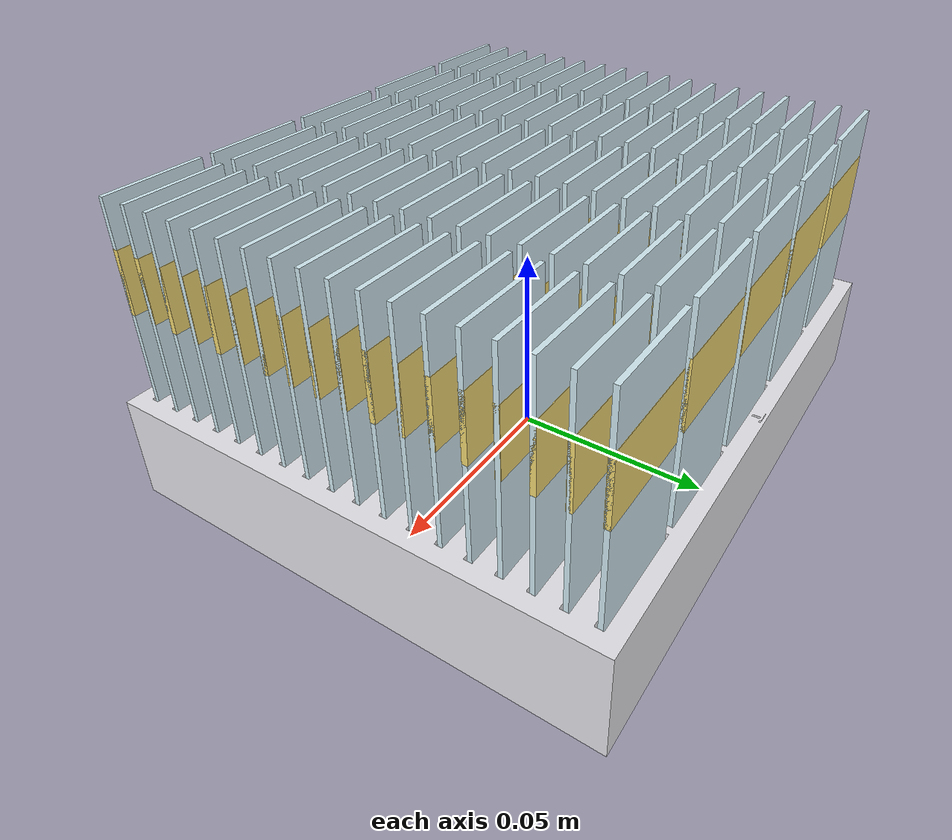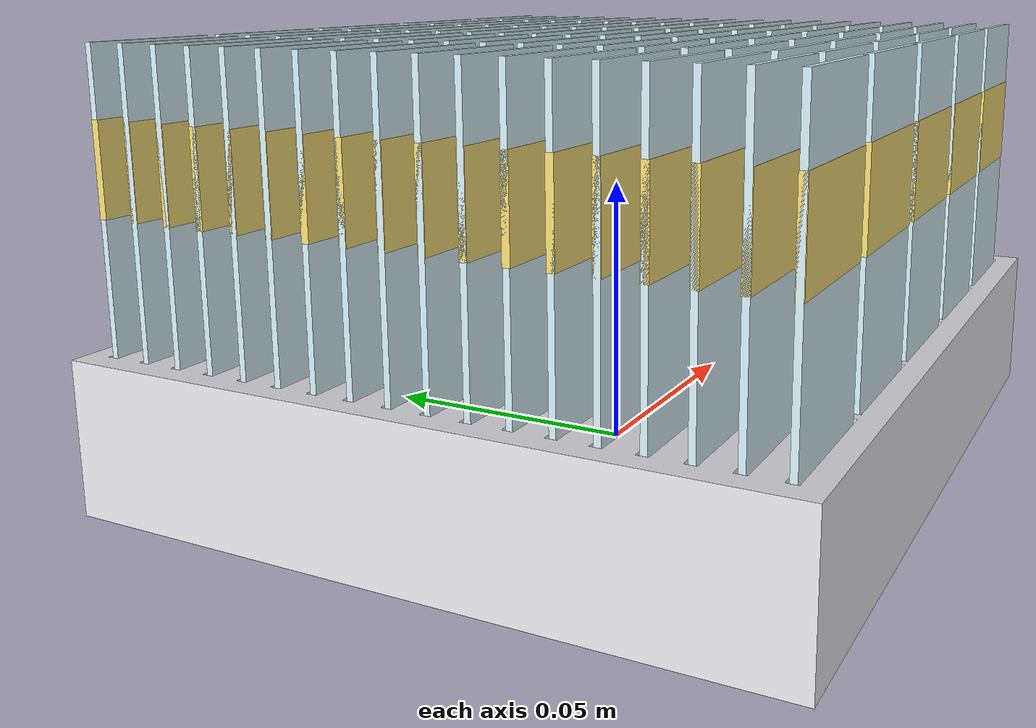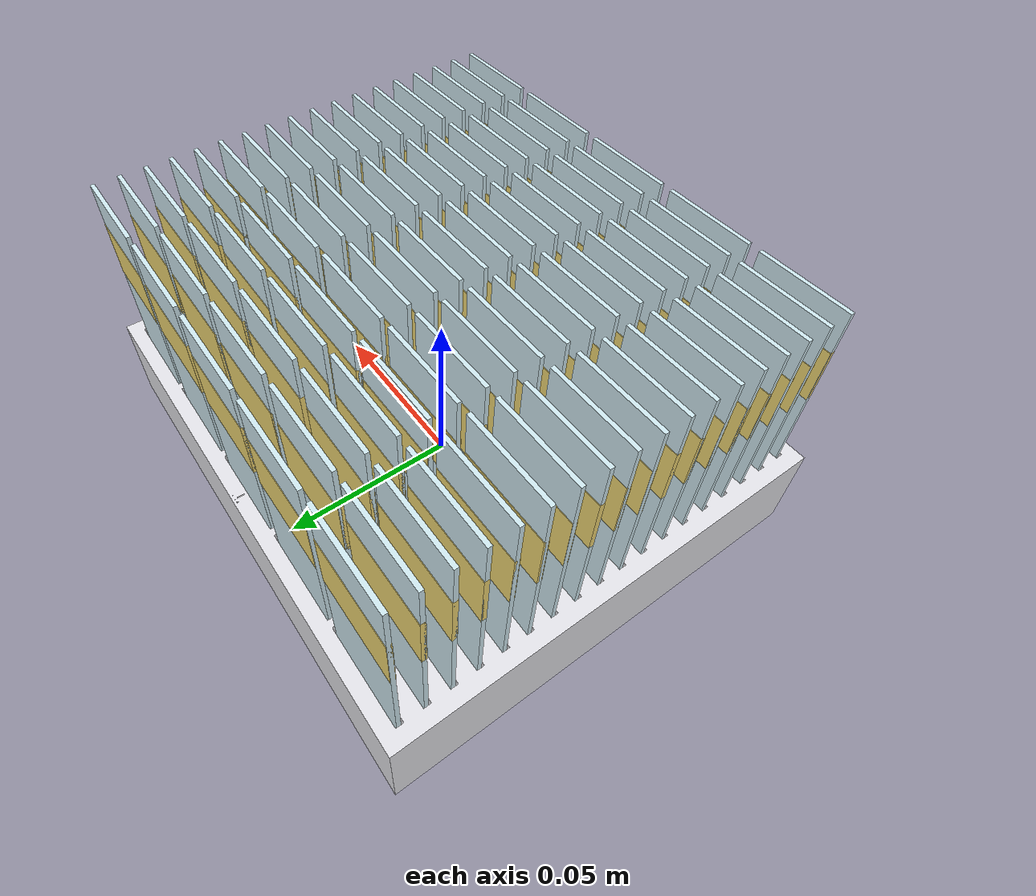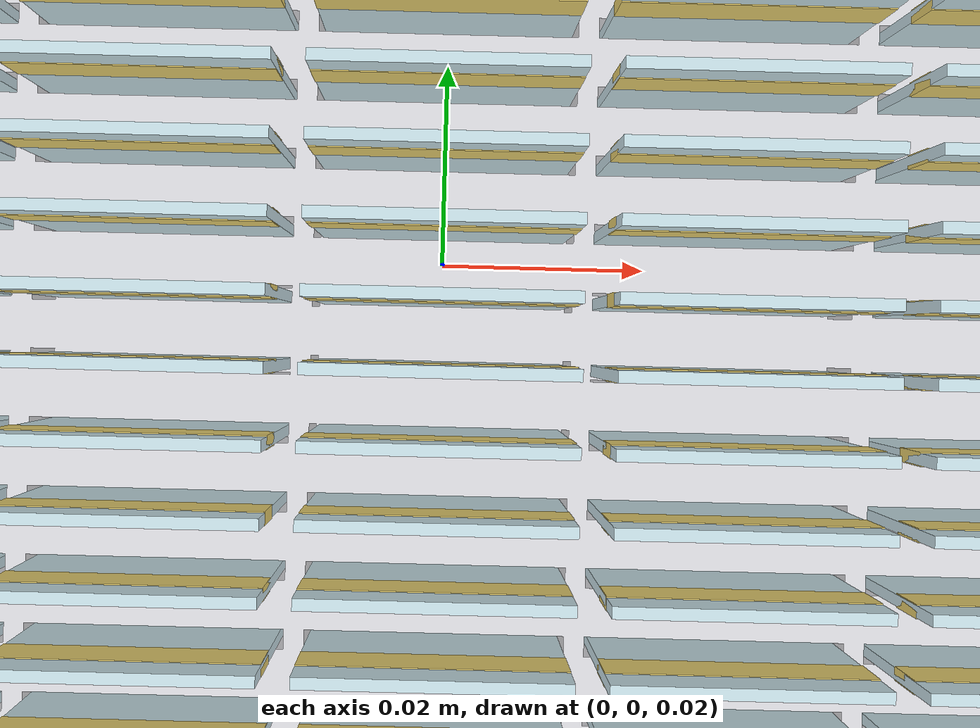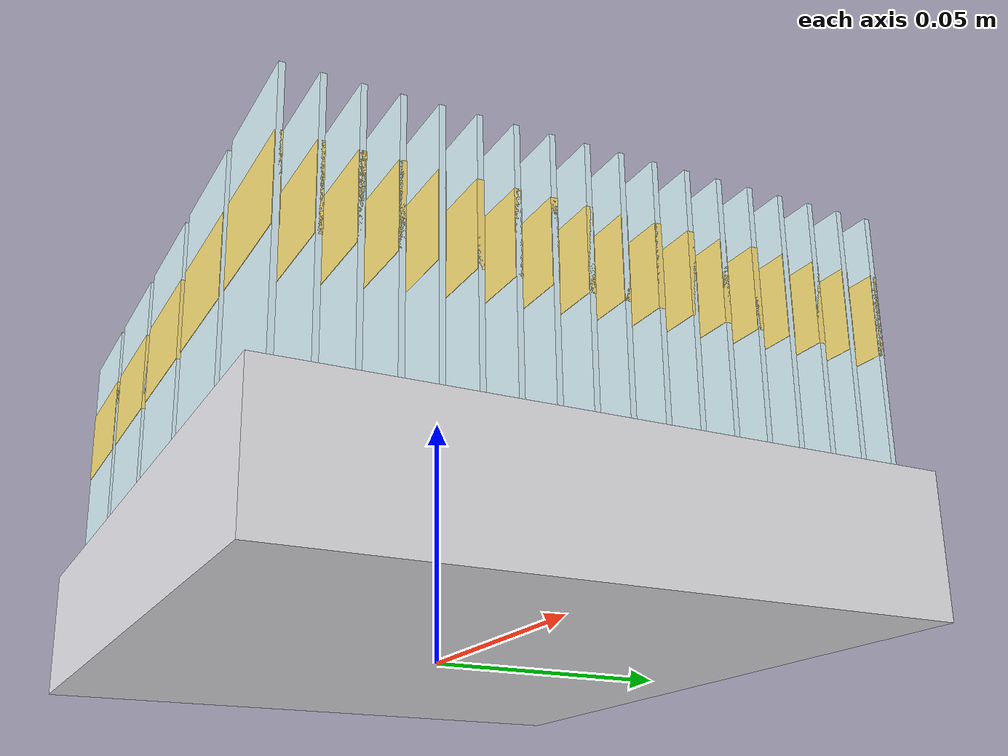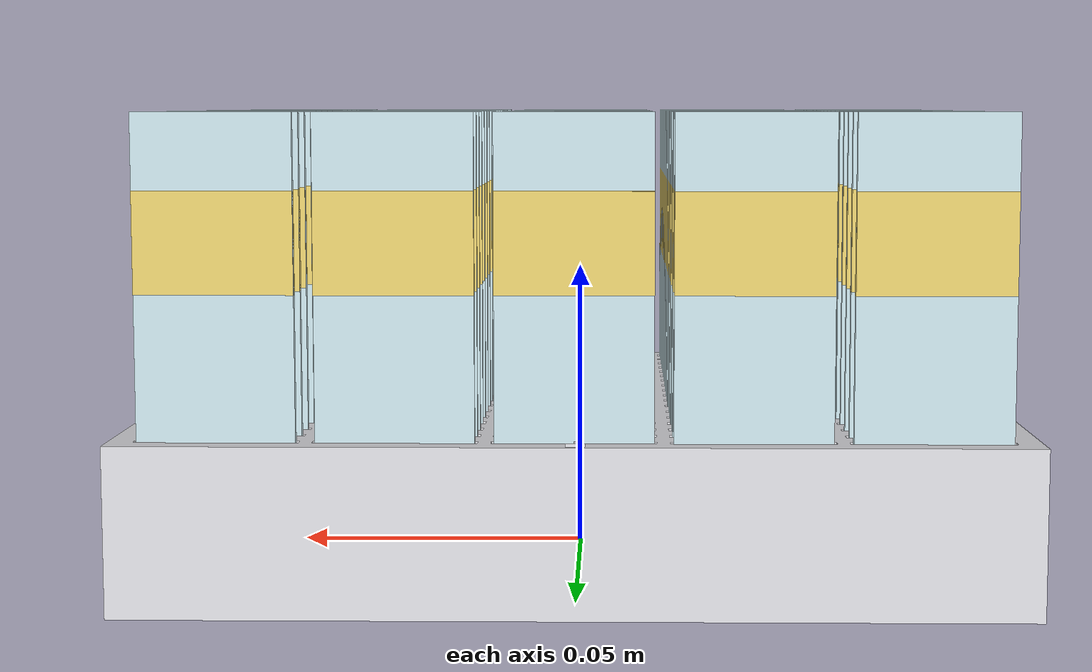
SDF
<?xml version="1.0" ?>
<sdf version="1.7">
  <model name="rack_laminillas_lleno">
    <static>true</static>
    <link name="link">

      <collision name="col_base">
        <pose>0.00000 0.00000 0.00100 0 0 0</pose>
        <geometry>
          <box><size>0.14450 0.12560 0.00200</size></box>
        </geometry>
        <surface>
          <friction><ode><mu>0.9</mu><mu2>0.9</mu2></ode></friction>
          <contact>
            <ode><kp>1e6</kp><kd>100</kd><min_depth>0.0002</min_depth></ode>
          </contact>
        </surface>
      </collision>

      <collision name="col_nervio_y_00">
        <pose>0.00000 -0.06080 0.01450 0 0 0</pose>
        <geometry>
          <box><size>0.14450 0.00400 0.02500</size></box>
        </geometry>
        <surface>
          <friction><ode><mu>0.9</mu><mu2>0.9</mu2></ode></friction>
          <contact>
            <ode><kp>1e6</kp><kd>100</kd><min_depth>0.0002</min_depth></ode>
          </contact>
        </surface>
      </collision>

      <collision name="col_nervio_y_01">
        <pose>0.00000 -0.05440 0.01450 0 0 0</pose>
        <geometry>
          <box><size>0.14450 0.00480 0.02500</size></box>
        </geometry>
        <surface>
          <friction><ode><mu>0.9</mu><mu2>0.9</mu2></ode></friction>
          <contact>
            <ode><kp>1e6</kp><kd>100</kd><min_depth>0.0002</min_depth></ode>
          </contact>
        </surface>
      </collision>

      <collision name="col_nervio_y_02">
        <pose>0.00000 -0.04760 0.01450 0 0 0</pose>
        <geometry>
          <box><size>0.14450 0.00480 0.02500</size></box>
        </geometry>
        <surface>
          <friction><ode><mu>0.9</mu><mu2>0.9</mu2></ode></friction>
          <contact>
            <ode><kp>1e6</kp><kd>100</kd><min_depth>0.0002</min_depth></ode>
          </contact>
        </surface>
      </collision>

      <collision name="col_nervio_y_03">
        <pose>0.00000 -0.04080 0.01450 0 0 0</pose>
        <geometry>
          <box><size>0.14450 0.00480 0.02500</size></box>
        </geometry>
        <surface>
          <friction><ode><mu>0.9</mu><mu2>0.9</mu2></ode></friction>
          <contact>
            <ode><kp>1e6</kp><kd>100</kd><min_depth>0.0002</min_depth></ode>
          </contact>
        </surface>
      </collision>

      <collision name="col_nervio_y_04">
        <pose>0.00000 -0.03400 0.01450 0 0 0</pose>
        <geometry>
          <box><size>0.14450 0.00480 0.02500</size></box>
        </geometry>
        <surface>
          <friction><ode><mu>0.9</mu><mu2>0.9</mu2></ode></friction>
          <contact>
            <ode><kp>1e6</kp><kd>100</kd><min_depth>0.0002</min_depth></ode>
          </contact>
        </surface>
      </collision>

      <collision name="col_nervio_y_05">
        <pose>0.00000 -0.02720 0.01450 0 0 0</pose>
        <geometry>
          <box><size>0.14450 0.00480 0.02500</size></box>
        </geometry>
        <surface>
          <friction><ode><mu>0.9</mu><mu2>0.9</mu2></ode></friction>
          <contact>
            <ode><kp>1e6</kp><kd>100</kd><min_depth>0.0002</min_depth></ode>
          </contact>
        </surface>
      </collision>

      <collision name="col_nervio_y_06">
        <pose>0.00000 -0.02040 0.01450 0 0 0</pose>
        <geometry>
          <box><size>0.14450 0.00480 0.02500</size></box>
        </geometry>
        <surface>
          <friction><ode><mu>0.9</mu><mu2>0.9</mu2></ode></friction>
          <contact>
            <ode><kp>1e6</kp><kd>100</kd><min_depth>0.0002</min_depth></ode>
          </contact>
        </surface>
      </collision>

      <collision name="col_nervio_y_07">
        <pose>0.00000 -0.01360 0.01450 0 0 0</pose>
        <geometry>
          <box><size>0.14450 0.00480 0.02500</size></box>
        </geometry>
        <surface>
          <friction><ode><mu>0.9</mu><mu2>0.9</mu2></ode></friction>
          <contact>
            <ode><kp>1e6</kp><kd>100</kd><min_depth>0.0002</min_depth></ode>
          </contact>
        </surface>
      </collision>

      <collision name="col_nervio_y_08">
        <pose>0.00000 -0.00680 0.01450 0 0 0</pose>
        <geometry>
          <box><size>0.14450 0.00480 0.02500</size></box>
        </geometry>
        <surface>
          <friction><ode><mu>0.9</mu><mu2>0.9</mu2></ode></friction>
          <contact>
            <ode><kp>1e6</kp><kd>100</kd><min_depth>0.0002</min_depth></ode>
          </contact>
        </surface>
      </collision>

      <collision name="col_nervio_y_09">
        <pose>0.00000 0.00000 0.01450 0 0 0</pose>
        <geometry>
          <box><size>0.14450 0.00480 0.02500</size></box>
        </geometry>
        <surface>
          <friction><ode><mu>0.9</mu><mu2>0.9</mu2></ode></friction>
          <contact>
            <ode><kp>1e6</kp><kd>100</kd><min_depth>0.0002</min_depth></ode>
          </contact>
        </surface>
      </collision>

      <collision name="col_nervio_y_10">
        <pose>0.00000 0.00680 0.01450 0 0 0</pose>
        <geometry>
          <box><size>0.14450 0.00480 0.02500</size></box>
        </geometry>
        <surface>
          <friction><ode><mu>0.9</mu><mu2>0.9</mu2></ode></friction>
          <contact>
            <ode><kp>1e6</kp><kd>100</kd><min_depth>0.0002</min_depth></ode>
          </contact>
        </surface>
      </collision>

      <collision name="col_nervio_y_11">
        <pose>0.00000 0.01360 0.01450 0 0 0</pose>
        <geometry>
          <box><size>0.14450 0.00480 0.02500</size></box>
        </geometry>
        <surface>
          <friction><ode><mu>0.9</mu><mu2>0.9</mu2></ode></friction>
          <contact>
            <ode><kp>1e6</kp><kd>100</kd><min_depth>0.0002</min_depth></ode>
          </contact>
        </surface>
      </collision>

      <collision name="col_nervio_y_12">
        <pose>0.00000 0.02040 0.01450 0 0 0</pose>
        <geometry>
          <box><size>0.14450 0.00480 0.02500</size></box>
        </geometry>
        <surface>
          <friction><ode><mu>0.9</mu><mu2>0.9</mu2></ode></friction>
          <contact>
            <ode><kp>1e6</kp><kd>100</kd><min_depth>0.0002</min_depth></ode>
          </contact>
        </surface>
      </collision>

      <collision name="col_nervio_y_13">
        <pose>0.00000 0.02720 0.01450 0 0 0</pose>
        <geometry>
          <box><size>0.14450 0.00480 0.02500</size></box>
        </geometry>
        <surface>
          <friction><ode><mu>0.9</mu><mu2>0.9</mu2></ode></friction>
          <contact>
            <ode><kp>1e6</kp><kd>100</kd><min_depth>0.0002</min_depth></ode>
          </contact>
        </surface>
      </collision>

      <collision name="col_nervio_y_14">
        <pose>0.00000 0.03400 0.01450 0 0 0</pose>
        <geometry>
          <box><size>0.14450 0.00480 0.02500</size></box>
        </geometry>
        <surface>
          <friction><ode><mu>0.9</mu><mu2>0.9</mu2></ode></friction>
          <contact>
            <ode><kp>1e6</kp><kd>100</kd><min_depth>0.0002</min_depth></ode>
          </contact>
        </surface>
      </collision>

      <collision name="col_nervio_y_15">
        <pose>0.00000 0.04080 0.01450 0 0 0</pose>
        <geometry>
          <box><size>0.14450 0.00480 0.02500</size></box>
        </geometry>
        <surface>
          <friction><ode><mu>0.9</mu><mu2>0.9</mu2></ode></friction>
          <contact>
            <ode><kp>1e6</kp><kd>100</kd><min_depth>0.0002</min_depth></ode>
          </contact>
        </surface>
      </collision>

      <collision name="col_nervio_y_16">
        <pose>0.00000 0.04760 0.01450 0 0 0</pose>
        <geometry>
          <box><size>0.14450 0.00480 0.02500</size></box>
        </geometry>
        <surface>
          <friction><ode><mu>0.9</mu><mu2>0.9</mu2></ode></friction>
          <contact>
            <ode><kp>1e6</kp><kd>100</kd><min_depth>0.0002</min_depth></ode>
          </contact>
        </surface>
      </collision>

      <collision name="col_nervio_y_17">
        <pose>0.00000 0.05440 0.01450 0 0 0</pose>
        <geometry>
          <box><size>0.14450 0.00480 0.02500</size></box>
        </geometry>
        <surface>
          <friction><ode><mu>0.9</mu><mu2>0.9</mu2></ode></friction>
          <contact>
            <ode><kp>1e6</kp><kd>100</kd><min_depth>0.0002</min_depth></ode>
          </contact>
        </surface>
      </collision>

      <collision name="col_nervio_y_18">
        <pose>0.00000 0.06080 0.01450 0 0 0</pose>
        <geometry>
          <box><size>0.14450 0.00400 0.02500</size></box>
        </geometry>
        <surface>
          <friction><ode><mu>0.9</mu><mu2>0.9</mu2></ode></friction>
          <contact>
            <ode><kp>1e6</kp><kd>100</kd><min_depth>0.0002</min_depth></ode>
          </contact>
        </surface>
      </collision>

      <collision name="col_tabique_x_00">
        <pose>-0.07025 0.00000 0.01450 0 0 0</pose>
        <geometry>
          <box><size>0.00400 0.12560 0.02500</size></box>
        </geometry>
        <surface>
          <friction><ode><mu>0.9</mu><mu2>0.9</mu2></ode></friction>
          <contact>
            <ode><kp>1e6</kp><kd>100</kd><min_depth>0.0002</min_depth></ode>
          </contact>
        </surface>
      </collision>

      <collision name="col_tabique_x_01">
        <pose>-0.04155 0.00000 0.01450 0 0 0</pose>
        <geometry>
          <box><size>0.00200 0.12560 0.02500</size></box>
        </geometry>
        <surface>
          <friction><ode><mu>0.9</mu><mu2>0.9</mu2></ode></friction>
          <contact>
            <ode><kp>1e6</kp><kd>100</kd><min_depth>0.0002</min_depth></ode>
          </contact>
        </surface>
      </collision>

      <collision name="col_tabique_x_02">
        <pose>-0.01385 0.00000 0.01450 0 0 0</pose>
        <geometry>
          <box><size>0.00200 0.12560 0.02500</size></box>
        </geometry>
        <surface>
          <friction><ode><mu>0.9</mu><mu2>0.9</mu2></ode></friction>
          <contact>
            <ode><kp>1e6</kp><kd>100</kd><min_depth>0.0002</min_depth></ode>
          </contact>
        </surface>
      </collision>

      <collision name="col_tabique_x_03">
        <pose>0.01385 0.00000 0.01450 0 0 0</pose>
        <geometry>
          <box><size>0.00200 0.12560 0.02500</size></box>
        </geometry>
        <surface>
          <friction><ode><mu>0.9</mu><mu2>0.9</mu2></ode></friction>
          <contact>
            <ode><kp>1e6</kp><kd>100</kd><min_depth>0.0002</min_depth></ode>
          </contact>
        </surface>
      </collision>

      <collision name="col_tabique_x_04">
        <pose>0.04155 0.00000 0.01450 0 0 0</pose>
        <geometry>
          <box><size>0.00200 0.12560 0.02500</size></box>
        </geometry>
        <surface>
          <friction><ode><mu>0.9</mu><mu2>0.9</mu2></ode></friction>
          <contact>
            <ode><kp>1e6</kp><kd>100</kd><min_depth>0.0002</min_depth></ode>
          </contact>
        </surface>
      </collision>

      <collision name="col_tabique_x_05">
        <pose>0.07025 0.00000 0.01450 0 0 0</pose>
        <geometry>
          <box><size>0.00400 0.12560 0.02500</size></box>
        </geometry>
        <surface>
          <friction><ode><mu>0.9</mu><mu2>0.9</mu2></ode></friction>
          <contact>
            <ode><kp>1e6</kp><kd>100</kd><min_depth>0.0002</min_depth></ode>
          </contact>
        </surface>
      </collision>

      <visual name="rack">
        <geometry>
          <mesh>
            <uri>model://rack_laminillas/meshes/rack_laminillas.stl</uri>
            <scale>0.001 0.001 0.001</scale>
          </mesh>
        </geometry>
        <material>
          <ambient>0.78 0.78 0.80 1</ambient>
          <diffuse>0.90 0.90 0.92 1</diffuse>
          <specular>0.2 0.2 0.2 1</specular>
        </material>
      </visual>

      <visual name="lam_1_1">
        <pose>-0.05540 -0.05780 0.03990 0 0 0</pose>
        <geometry>
          <box><size>0.02470 0.00110 0.07580</size></box>
        </geometry>
        <material>
          <ambient>0.70 0.82 0.85 1</ambient>
          <diffuse>0.82 0.92 0.95 1</diffuse>
          <specular>0.4 0.4 0.4 1</specular>
        </material>
      </visual>
      <visual name="etq_1_1">
        <pose>-0.05540 -0.05780 0.05780 0 0 0</pose>
        <geometry>
          <box><size>0.02470 0.00130 0.01600</size></box>
        </geometry>
        <material>
          <ambient>0.85 0.75 0.35 1</ambient>
          <diffuse>0.95 0.85 0.45 1</diffuse>
        </material>
      </visual>

      <visual name="lam_1_2">
        <pose>-0.05540 -0.05100 0.03990 0 0 0</pose>
        <geometry>
          <box><size>0.02470 0.00110 0.07580</size></box>
        </geometry>
        <material>
          <ambient>0.70 0.82 0.85 1</ambient>
          <diffuse>0.82 0.92 0.95 1</diffuse>
          <specular>0.4 0.4 0.4 1</specular>
        </material>
      </visual>
      <visual name="etq_1_2">
        <pose>-0.05540 -0.05100 0.05780 0 0 0</pose>
        <geometry>
          <box><size>0.02470 0.00130 0.01600</size></box>
        </geometry>
        <material>
          <ambient>0.85 0.75 0.35 1</ambient>
          <diffuse>0.95 0.85 0.45 1</diffuse>
        </material>
      </visual>

      <visual name="lam_1_3">
        <pose>-0.05540 -0.04420 0.03990 0 0 0</pose>
        <geometry>
          <box><size>0.02470 0.00110 0.07580</size></box>
        </geometry>
        <material>
          <ambient>0.70 0.82 0.85 1</ambient>
          <diffuse>0.82 0.92 0.95 1</diffuse>
          <specular>0.4 0.4 0.4 1</specular>
        </material>
      </visual>
      <visual name="etq_1_3">
        <pose>-0.05540 -0.04420 0.05780 0 0 0</pose>
        <geometry>
          <box><size>0.02470 0.00130 0.01600</size></box>
        </geometry>
        <material>
          <ambient>0.85 0.75 0.35 1</ambient>
          <diffuse>0.95 0.85 0.45 1</diffuse>
        </material>
      </visual>

      <visual name="lam_1_4">
        <pose>-0.05540 -0.03740 0.03990 0 0 0</pose>
        <geometry>
          <box><size>0.02470 0.00110 0.07580</size></box>
        </geometry>
        <material>
          <ambient>0.70 0.82 0.85 1</ambient>
          <diffuse>0.82 0.92 0.95 1</diffuse>
          <specular>0.4 0.4 0.4 1</specular>
        </material>
      </visual>
      <visual name="etq_1_4">
        <pose>-0.05540 -0.03740 0.05780 0 0 0</pose>
        <geometry>
          <box><size>0.02470 0.00130 0.01600</size></box>
        </geometry>
        <material>
          <ambient>0.85 0.75 0.35 1</ambient>
          <diffuse>0.95 0.85 0.45 1</diffuse>
        </material>
      </visual>

      <visual name="lam_1_5">
        <pose>-0.05540 -0.03060 0.03990 0 0 0</pose>
        <geometry>
          <box><size>0.02470 0.00110 0.07580</size></box>
        </geometry>
        <material>
          <ambient>0.70 0.82 0.85 1</ambient>
          <diffuse>0.82 0.92 0.95 1</diffuse>
          <specular>0.4 0.4 0.4 1</specular>
        </material>
      </visual>
      <visual name="etq_1_5">
        <pose>-0.05540 -0.03060 0.05780 0 0 0</pose>
        <geometry>
          <box><size>0.02470 0.00130 0.01600</size></box>
        </geometry>
        <material>
          <ambient>0.85 0.75 0.35 1</ambient>
          <diffuse>0.95 0.85 0.45 1</diffuse>
        </material>
      </visual>

      <visual name="lam_1_6">
        <pose>-0.05540 -0.02380 0.03990 0 0 0</pose>
        <geometry>
          <box><size>0.02470 0.00110 0.07580</size></box>
        </geometry>
        <material>
          <ambient>0.70 0.82 0.85 1</ambient>
          <diffuse>0.82 0.92 0.95 1</diffuse>
          <specular>0.4 0.4 0.4 1</specular>
        </material>
      </visual>
      <visual name="etq_1_6">
        <pose>-0.05540 -0.02380 0.05780 0 0 0</pose>
        <geometry>
          <box><size>0.02470 0.00130 0.01600</size></box>
        </geometry>
        <material>
          <ambient>0.85 0.75 0.35 1</ambient>
          <diffuse>0.95 0.85 0.45 1</diffuse>
        </material>
      </visual>

      <visual name="lam_1_7">
        <pose>-0.05540 -0.01700 0.03990 0 0 0</pose>
        <geometry>
          <box><size>0.02470 0.00110 0.07580</size></box>
        </geometry>
        <material>
          <ambient>0.70 0.82 0.85 1</ambient>
          <diffuse>0.82 0.92 0.95 1</diffuse>
          <specular>0.4 0.4 0.4 1</specular>
        </material>
      </visual>
      <visual name="etq_1_7">
        <pose>-0.05540 -0.01700 0.05780 0 0 0</pose>
        <geometry>
          <box><size>0.02470 0.00130 0.01600</size></box>
        </geometry>
        <material>
          <ambient>0.85 0.75 0.35 1</ambient>
          <diffuse>0.95 0.85 0.45 1</diffuse>
        </material>
      </visual>

      <visual name="lam_1_8">
        <pose>-0.05540 -0.01020 0.03990 0 0 0</pose>
        <geometry>
          <box><size>0.02470 0.00110 0.07580</size></box>
        </geometry>
        <material>
          <ambient>0.70 0.82 0.85 1</ambient>
          <diffuse>0.82 0.92 0.95 1</diffuse>
          <specular>0.4 0.4 0.4 1</specular>
        </material>
      </visual>
      <visual name="etq_1_8">
        <pose>-0.05540 -0.01020 0.05780 0 0 0</pose>
        <geometry>
          <box><size>0.02470 0.00130 0.01600</size></box>
        </geometry>
        <material>
          <ambient>0.85 0.75 0.35 1</ambient>
          <diffuse>0.95 0.85 0.45 1</diffuse>
        </material>
      </visual>

      <visual name="lam_1_9">
        <pose>-0.05540 -0.00340 0.03990 0 0 0</pose>
        <geometry>
          <box><size>0.02470 0.00110 0.07580</size></box>
        </geometry>
        <material>
          <ambient>0.70 0.82 0.85 1</ambient>
          <diffuse>0.82 0.92 0.95 1</diffuse>
          <specular>0.4 0.4 0.4 1</specular>
        </material>
      </visual>
      <visual name="etq_1_9">
        <pose>-0.05540 -0.00340 0.05780 0 0 0</pose>
        <geometry>
          <box><size>0.02470 0.00130 0.01600</size></box>
        </geometry>
        <material>
          <ambient>0.85 0.75 0.35 1</ambient>
          <diffuse>0.95 0.85 0.45 1</diffuse>
        </material>
      </visual>

      <visual name="lam_1_10">
        <pose>-0.05540 0.00340 0.03990 0 0 0</pose>
        <geometry>
          <box><size>0.02470 0.00110 0.07580</size></box>
        </geometry>
        <material>
          <ambient>0.70 0.82 0.85 1</ambient>
          <diffuse>0.82 0.92 0.95 1</diffuse>
          <specular>0.4 0.4 0.4 1</specular>
        </material>
      </visual>
      <visual name="etq_1_10">
        <pose>-0.05540 0.00340 0.05780 0 0 0</pose>
        <geometry>
          <box><size>0.02470 0.00130 0.01600</size></box>
        </geometry>
        <material>
          <ambient>0.85 0.75 0.35 1</ambient>
          <diffuse>0.95 0.85 0.45 1</diffuse>
        </material>
      </visual>

      <visual name="lam_1_11">
        <pose>-0.05540 0.01020 0.03990 0 0 0</pose>
        <geometry>
          <box><size>0.02470 0.00110 0.07580</size></box>
        </geometry>
        <material>
          <ambient>0.70 0.82 0.85 1</ambient>
          <diffuse>0.82 0.92 0.95 1</diffuse>
          <specular>0.4 0.4 0.4 1</specular>
        </material>
      </visual>
      <visual name="etq_1_11">
        <pose>-0.05540 0.01020 0.05780 0 0 0</pose>
        <geometry>
          <box><size>0.02470 0.00130 0.01600</size></box>
        </geometry>
        <material>
          <ambient>0.85 0.75 0.35 1</ambient>
          <diffuse>0.95 0.85 0.45 1</diffuse>
        </material>
      </visual>

      <visual name="lam_1_12">
        <pose>-0.05540 0.01700 0.03990 0 0 0</pose>
        <geometry>
          <box><size>0.02470 0.00110 0.07580</size></box>
        </geometry>
        <material>
          <ambient>0.70 0.82 0.85 1</ambient>
          <diffuse>0.82 0.92 0.95 1</diffuse>
          <specular>0.4 0.4 0.4 1</specular>
        </material>
      </visual>
      <visual name="etq_1_12">
        <pose>-0.05540 0.01700 0.05780 0 0 0</pose>
        <geometry>
          <box><size>0.02470 0.00130 0.01600</size></box>
        </geometry>
        <material>
          <ambient>0.85 0.75 0.35 1</ambient>
          <diffuse>0.95 0.85 0.45 1</diffuse>
        </material>
      </visual>

      <visual name="lam_1_13">
        <pose>-0.05540 0.02380 0.03990 0 0 0</pose>
        <geometry>
          <box><size>0.02470 0.00110 0.07580</size></box>
        </geometry>
        <material>
          <ambient>0.70 0.82 0.85 1</ambient>
          <diffuse>0.82 0.92 0.95 1</diffuse>
          <specular>0.4 0.4 0.4 1</specular>
        </material>
      </visual>
      <visual name="etq_1_13">
        <pose>-0.05540 0.02380 0.05780 0 0 0</pose>
        <geometry>
          <box><size>0.02470 0.00130 0.01600</size></box>
        </geometry>
        <material>
          <ambient>0.85 0.75 0.35 1</ambient>
          <diffuse>0.95 0.85 0.45 1</diffuse>
        </material>
      </visual>

      <visual name="lam_1_14">
        <pose>-0.05540 0.03060 0.03990 0 0 0</pose>
        <geometry>
          <box><size>0.02470 0.00110 0.07580</size></box>
        </geometry>
        <material>
          <ambient>0.70 0.82 0.85 1</ambient>
          <diffuse>0.82 0.92 0.95 1</diffuse>
          <specular>0.4 0.4 0.4 1</specular>
        </material>
      </visual>
      <visual name="etq_1_14">
        <pose>-0.05540 0.03060 0.05780 0 0 0</pose>
        <geometry>
          <box><size>0.02470 0.00130 0.01600</size></box>
        </geometry>
        <material>
          <ambient>0.85 0.75 0.35 1</ambient>
          <diffuse>0.95 0.85 0.45 1</diffuse>
        </material>
      </visual>

      <visual name="lam_1_15">
        <pose>-0.05540 0.03740 0.03990 0 0 0</pose>
        <geometry>
          <box><size>0.02470 0.00110 0.07580</size></box>
        </geometry>
        <material>
          <ambient>0.70 0.82 0.85 1</ambient>
          <diffuse>0.82 0.92 0.95 1</diffuse>
          <specular>0.4 0.4 0.4 1</specular>
        </material>
      </visual>
      <visual name="etq_1_15">
        <pose>-0.05540 0.03740 0.05780 0 0 0</pose>
        <geometry>
          <box><size>0.02470 0.00130 0.01600</size></box>
        </geometry>
        <material>
          <ambient>0.85 0.75 0.35 1</ambient>
          <diffuse>0.95 0.85 0.45 1</diffuse>
        </material>
      </visual>

      <visual name="lam_1_16">
        <pose>-0.05540 0.04420 0.03990 0 0 0</pose>
        <geometry>
          <box><size>0.02470 0.00110 0.07580</size></box>
        </geometry>
        <material>
          <ambient>0.70 0.82 0.85 1</ambient>
          <diffuse>0.82 0.92 0.95 1</diffuse>
          <specular>0.4 0.4 0.4 1</specular>
        </material>
      </visual>
      <visual name="etq_1_16">
        <pose>-0.05540 0.04420 0.05780 0 0 0</pose>
        <geometry>
          <box><size>0.02470 0.00130 0.01600</size></box>
        </geometry>
        <material>
          <ambient>0.85 0.75 0.35 1</ambient>
          <diffuse>0.95 0.85 0.45 1</diffuse>
        </material>
      </visual>

      <visual name="lam_1_17">
        <pose>-0.05540 0.05100 0.03990 0 0 0</pose>
        <geometry>
          <box><size>0.02470 0.00110 0.07580</size></box>
        </geometry>
        <material>
          <ambient>0.70 0.82 0.85 1</ambient>
          <diffuse>0.82 0.92 0.95 1</diffuse>
          <specular>0.4 0.4 0.4 1</specular>
        </material>
      </visual>
      <visual name="etq_1_17">
        <pose>-0.05540 0.05100 0.05780 0 0 0</pose>
        <geometry>
          <box><size>0.02470 0.00130 0.01600</size></box>
        </geometry>
        <material>
          <ambient>0.85 0.75 0.35 1</ambient>
          <diffuse>0.95 0.85 0.45 1</diffuse>
        </material>
      </visual>

      <visual name="lam_1_18">
        <pose>-0.05540 0.05780 0.03990 0 0 0</pose>
        <geometry>
          <box><size>0.02470 0.00110 0.07580</size></box>
        </geometry>
        <material>
          <ambient>0.70 0.82 0.85 1</ambient>
          <diffuse>0.82 0.92 0.95 1</diffuse>
          <specular>0.4 0.4 0.4 1</specular>
        </material>
      </visual>
      <visual name="etq_1_18">
        <pose>-0.05540 0.05780 0.05780 0 0 0</pose>
        <geometry>
          <box><size>0.02470 0.00130 0.01600</size></box>
        </geometry>
        <material>
          <ambient>0.85 0.75 0.35 1</ambient>
          <diffuse>0.95 0.85 0.45 1</diffuse>
        </material>
      </visual>

      <visual name="lam_2_1">
        <pose>-0.02770 -0.05780 0.03990 0 0 0</pose>
        <geometry>
          <box><size>0.02470 0.00110 0.07580</size></box>
        </geometry>
        <material>
          <ambient>0.70 0.82 0.85 1</ambient>
          <diffuse>0.82 0.92 0.95 1</diffuse>
          <specular>0.4 0.4 0.4 1</specular>
        </material>
      </visual>
      <visual name="etq_2_1">
        <pose>-0.02770 -0.05780 0.05780 0 0 0</pose>
        <geometry>
          <box><size>0.02470 0.00130 0.01600</size></box>
        </geometry>
        <material>
          <ambient>0.85 0.75 0.35 1</ambient>
          <diffuse>0.95 0.85 0.45 1</diffuse>
        </material>
      </visual>

      <visual name="lam_2_2">
        <pose>-0.02770 -0.05100 0.03990 0 0 0</pose>
        <geometry>
          <box><size>0.02470 0.00110 0.07580</size></box>
        </geometry>
        <material>
          <ambient>0.70 0.82 0.85 1</ambient>
          <diffuse>0.82 0.92 0.95 1</diffuse>
          <specular>0.4 0.4 0.4 1</specular>
        </material>
      </visual>
      <visual name="etq_2_2">
        <pose>-0.02770 -0.05100 0.05780 0 0 0</pose>
        <geometry>
          <box><size>0.02470 0.00130 0.01600</size></box>
        </geometry>
        <material>
          <ambient>0.85 0.75 0.35 1</ambient>
          <diffuse>0.95 0.85 0.45 1</diffuse>
        </material>
      </visual>

      <visual name="lam_2_3">
        <pose>-0.02770 -0.04420 0.03990 0 0 0</pose>
        <geometry>
          <box><size>0.02470 0.00110 0.07580</size></box>
        </geometry>
        <material>
          <ambient>0.70 0.82 0.85 1</ambient>
          <diffuse>0.82 0.92 0.95 1</diffuse>
          <specular>0.4 0.4 0.4 1</specular>
        </material>
      </visual>
      <visual name="etq_2_3">
        <pose>-0.02770 -0.04420 0.05780 0 0 0</pose>
        <geometry>
          <box><size>0.02470 0.00130 0.01600</size></box>
        </geometry>
        <material>
          <ambient>0.85 0.75 0.35 1</ambient>
          <diffuse>0.95 0.85 0.45 1</diffuse>
        </material>
      </visual>

      <visual name="lam_2_4">
        <pose>-0.02770 -0.03740 0.03990 0 0 0</pose>
        <geometry>
          <box><size>0.02470 0.00110 0.07580</size></box>
        </geometry>
        <material>
          <ambient>0.70 0.82 0.85 1</ambient>
          <diffuse>0.82 0.92 0.95 1</diffuse>
          <specular>0.4 0.4 0.4 1</specular>
        </material>
      </visual>
      <visual name="etq_2_4">
        <pose>-0.02770 -0.03740 0.05780 0 0 0</pose>
        <geometry>
          <box><size>0.02470 0.00130 0.01600</size></box>
        </geometry>
        <material>
          <ambient>0.85 0.75 0.35 1</ambient>
          <diffuse>0.95 0.85 0.45 1</diffuse>
        </material>
      </visual>

      <visual name="lam_2_5">
        <pose>-0.02770 -0.03060 0.03990 0 0 0</pose>
        <geometry>
          <box><size>0.02470 0.00110 0.07580</size></box>
        </geometry>
        <material>
          <ambient>0.70 0.82 0.85 1</ambient>
          <diffuse>0.82 0.92 0.95 1</diffuse>
          <specular>0.4 0.4 0.4 1</specular>
        </material>
      </visual>
      <visual name="etq_2_5">
        <pose>-0.02770 -0.03060 0.05780 0 0 0</pose>
        <geometry>
          <box><size>0.02470 0.00130 0.01600</size></box>
        </geometry>
        <material>
          <ambient>0.85 0.75 0.35 1</ambient>
          <diffuse>0.95 0.85 0.45 1</diffuse>
        </material>
      </visual>

      <visual name="lam_2_6">
        <pose>-0.02770 -0.02380 0.03990 0 0 0</pose>
        <geometry>
          <box><size>0.02470 0.00110 0.07580</size></box>
        </geometry>
        <material>
          <ambient>0.70 0.82 0.85 1</ambient>
          <diffuse>0.82 0.92 0.95 1</diffuse>
          <specular>0.4 0.4 0.4 1</specular>
        </material>
      </visual>
      <visual name="etq_2_6">
        <pose>-0.02770 -0.02380 0.05780 0 0 0</pose>
        <geometry>
          <box><size>0.02470 0.00130 0.01600</size></box>
        </geometry>
        <material>
          <ambient>0.85 0.75 0.35 1</ambient>
          <diffuse>0.95 0.85 0.45 1</diffuse>
        </material>
      </visual>

      <visual name="lam_2_7">
        <pose>-0.02770 -0.01700 0.03990 0 0 0</pose>
        <geometry>
          <box><size>0.02470 0.00110 0.07580</size></box>
        </geometry>
        <material>
          <ambient>0.70 0.82 0.85 1</ambient>
          <diffuse>0.82 0.92 0.95 1</diffuse>
          <specular>0.4 0.4 0.4 1</specular>
        </material>
      </visual>
      <visual name="etq_2_7">
        <pose>-0.02770 -0.01700 0.05780 0 0 0</pose>
        <geometry>
          <box><size>0.02470 0.00130 0.01600</size></box>
        </geometry>
        <material>
          <ambient>0.85 0.75 0.35 1</ambient>
          <diffuse>0.95 0.85 0.45 1</diffuse>
        </material>
      </visual>

      <visual name="lam_2_8">
        <pose>-0.02770 -0.01020 0.03990 0 0 0</pose>
        <geometry>
          <box><size>0.02470 0.00110 0.07580</size></box>
        </geometry>
        <material>
          <ambient>0.70 0.82 0.85 1</ambient>
          <diffuse>0.82 0.92 0.95 1</diffuse>
          <specular>0.4 0.4 0.4 1</specular>
        </material>
      </visual>
      <visual name="etq_2_8">
        <pose>-0.02770 -0.01020 0.05780 0 0 0</pose>
        <geometry>
          <box><size>0.02470 0.00130 0.01600</size></box>
        </geometry>
        <material>
          <ambient>0.85 0.75 0.35 1</ambient>
          <diffuse>0.95 0.85 0.45 1</diffuse>
        </material>
      </visual>

      <visual name="lam_2_9">
        <pose>-0.02770 -0.00340 0.03990 0 0 0</pose>
        <geometry>
          <box><size>0.02470 0.00110 0.07580</size></box>
        </geometry>
        <material>
          <ambient>0.70 0.82 0.85 1</ambient>
          <diffuse>0.82 0.92 0.95 1</diffuse>
          <specular>0.4 0.4 0.4 1</specular>
        </material>
      </visual>
      <visual name="etq_2_9">
        <pose>-0.02770 -0.00340 0.05780 0 0 0</pose>
        <geometry>
          <box><size>0.02470 0.00130 0.01600</size></box>
        </geometry>
        <material>
          <ambient>0.85 0.75 0.35 1</ambient>
          <diffuse>0.95 0.85 0.45 1</diffuse>
        </material>
      </visual>

      <visual name="lam_2_10">
        <pose>-0.02770 0.00340 0.03990 0 0 0</pose>
        <geometry>
          <box><size>0.02470 0.00110 0.07580</size></box>
        </geometry>
        <material>
          <ambient>0.70 0.82 0.85 1</ambient>
          <diffuse>0.82 0.92 0.95 1</diffuse>
          <specular>0.4 0.4 0.4 1</specular>
        </material>
      </visual>
      <visual name="etq_2_10">
        <pose>-0.02770 0.00340 0.05780 0 0 0</pose>
        <geometry>
          <box><size>0.02470 0.00130 0.01600</size></box>
        </geometry>
        <material>
          <ambient>0.85 0.75 0.35 1</ambient>
          <diffuse>0.95 0.85 0.45 1</diffuse>
        </material>
      </visual>

      <visual name="lam_2_11">
        <pose>-0.02770 0.01020 0.03990 0 0 0</pose>
        <geometry>
          <box><size>0.02470 0.00110 0.07580</size></box>
        </geometry>
        <material>
          <ambient>0.70 0.82 0.85 1</ambient>
          <diffuse>0.82 0.92 0.95 1</diffuse>
          <specular>0.4 0.4 0.4 1</specular>
        </material>
      </visual>
      <visual name="etq_2_11">
        <pose>-0.02770 0.01020 0.05780 0 0 0</pose>
        <geometry>
          <box><size>0.02470 0.00130 0.01600</size></box>
        </geometry>
        <material>
          <ambient>0.85 0.75 0.35 1</ambient>
          <diffuse>0.95 0.85 0.45 1</diffuse>
        </material>
      </visual>

      <visual name="lam_2_12">
        <pose>-0.02770 0.01700 0.03990 0 0 0</pose>
        <geometry>
          <box><size>0.02470 0.00110 0.07580</size></box>
        </geometry>
        <material>
          <ambient>0.70 0.82 0.85 1</ambient>
          <diffuse>0.82 0.92 0.95 1</diffuse>
          <specular>0.4 0.4 0.4 1</specular>
        </material>
      </visual>
      <visual name="etq_2_12">
        <pose>-0.02770 0.01700 0.05780 0 0 0</pose>
        <geometry>
          <box><size>0.02470 0.00130 0.01600</size></box>
        </geometry>
        <material>
          <ambient>0.85 0.75 0.35 1</ambient>
          <diffuse>0.95 0.85 0.45 1</diffuse>
        </material>
      </visual>

      <visual name="lam_2_13">
        <pose>-0.02770 0.02380 0.03990 0 0 0</pose>
        <geometry>
          <box><size>0.02470 0.00110 0.07580</size></box>
        </geometry>
        <material>
          <ambient>0.70 0.82 0.85 1</ambient>
          <diffuse>0.82 0.92 0.95 1</diffuse>
          <specular>0.4 0.4 0.4 1</specular>
        </material>
      </visual>
      <visual name="etq_2_13">
        <pose>-0.02770 0.02380 0.05780 0 0 0</pose>
        <geometry>
          <box><size>0.02470 0.00130 0.01600</size></box>
        </geometry>
        <material>
          <ambient>0.85 0.75 0.35 1</ambient>
          <diffuse>0.95 0.85 0.45 1</diffuse>
        </material>
      </visual>

      <visual name="lam_2_14">
        <pose>-0.02770 0.03060 0.03990 0 0 0</pose>
        <geometry>
          <box><size>0.02470 0.00110 0.07580</size></box>
        </geometry>
        <material>
          <ambient>0.70 0.82 0.85 1</ambient>
          <diffuse>0.82 0.92 0.95 1</diffuse>
          <specular>0.4 0.4 0.4 1</specular>
        </material>
      </visual>
      <visual name="etq_2_14">
        <pose>-0.02770 0.03060 0.05780 0 0 0</pose>
        <geometry>
          <box><size>0.02470 0.00130 0.01600</size></box>
        </geometry>
        <material>
          <ambient>0.85 0.75 0.35 1</ambient>
          <diffuse>0.95 0.85 0.45 1</diffuse>
        </material>
      </visual>

      <visual name="lam_2_15">
        <pose>-0.02770 0.03740 0.03990 0 0 0</pose>
        <geometry>
          <box><size>0.02470 0.00110 0.07580</size></box>
        </geometry>
        <material>
          <ambient>0.70 0.82 0.85 1</ambient>
          <diffuse>0.82 0.92 0.95 1</diffuse>
          <specular>0.4 0.4 0.4 1</specular>
        </material>
      </visual>
      <visual name="etq_2_15">
        <pose>-0.02770 0.03740 0.05780 0 0 0</pose>
        <geometry>
          <box><size>0.02470 0.00130 0.01600</size></box>
        </geometry>
        <material>
          <ambient>0.85 0.75 0.35 1</ambient>
          <diffuse>0.95 0.85 0.45 1</diffuse>
        </material>
      </visual>

      <visual name="lam_2_16">
        <pose>-0.02770 0.04420 0.03990 0 0 0</pose>
        <geometry>
          <box><size>0.02470 0.00110 0.07580</size></box>
        </geometry>
        <material>
          <ambient>0.70 0.82 0.85 1</ambient>
          <diffuse>0.82 0.92 0.95 1</diffuse>
          <specular>0.4 0.4 0.4 1</specular>
        </material>
      </visual>
      <visual name="etq_2_16">
        <pose>-0.02770 0.04420 0.05780 0 0 0</pose>
        <geometry>
          <box><size>0.02470 0.00130 0.01600</size></box>
        </geometry>
        <material>
          <ambient>0.85 0.75 0.35 1</ambient>
          <diffuse>0.95 0.85 0.45 1</diffuse>
        </material>
      </visual>

      <visual name="lam_2_17">
        <pose>-0.02770 0.05100 0.03990 0 0 0</pose>
        <geometry>
          <box><size>0.02470 0.00110 0.07580</size></box>
        </geometry>
        <material>
          <ambient>0.70 0.82 0.85 1</ambient>
          <diffuse>0.82 0.92 0.95 1</diffuse>
          <specular>0.4 0.4 0.4 1</specular>
        </material>
      </visual>
      <visual name="etq_2_17">
        <pose>-0.02770 0.05100 0.05780 0 0 0</pose>
        <geometry>
          <box><size>0.02470 0.00130 0.01600</size></box>
        </geometry>
        <material>
          <ambient>0.85 0.75 0.35 1</ambient>
          <diffuse>0.95 0.85 0.45 1</diffuse>
        </material>
      </visual>

      <visual name="lam_2_18">
        <pose>-0.02770 0.05780 0.03990 0 0 0</pose>
        <geometry>
          <box><size>0.02470 0.00110 0.07580</size></box>
        </geometry>
        <material>
          <ambient>0.70 0.82 0.85 1</ambient>
          <diffuse>0.82 0.92 0.95 1</diffuse>
          <specular>0.4 0.4 0.4 1</specular>
        </material>
      </visual>
      <visual name="etq_2_18">
        <pose>-0.02770 0.05780 0.05780 0 0 0</pose>
        <geometry>
          <box><size>0.02470 0.00130 0.01600</size></box>
        </geometry>
        <material>
          <ambient>0.85 0.75 0.35 1</ambient>
          <diffuse>0.95 0.85 0.45 1</diffuse>
        </material>
      </visual>

      <visual name="lam_3_1">
        <pose>0.00000 -0.05780 0.03990 0 0 0</pose>
        <geometry>
          <box><size>0.02470 0.00110 0.07580</size></box>
        </geometry>
        <material>
          <ambient>0.70 0.82 0.85 1</ambient>
          <diffuse>0.82 0.92 0.95 1</diffuse>
          <specular>0.4 0.4 0.4 1</specular>
        </material>
      </visual>
      <visual name="etq_3_1">
        <pose>0.00000 -0.05780 0.05780 0 0 0</pose>
        <geometry>
          <box><size>0.02470 0.00130 0.01600</size></box>
        </geometry>
        <material>
          <ambient>0.85 0.75 0.35 1</ambient>
          <diffuse>0.95 0.85 0.45 1</diffuse>
        </material>
      </visual>

      <visual name="lam_3_2">
        <pose>0.00000 -0.05100 0.03990 0 0 0</pose>
        <geometry>
          <box><size>0.02470 0.00110 0.07580</size></box>
        </geometry>
        <material>
          <ambient>0.70 0.82 0.85 1</ambient>
          <diffuse>0.82 0.92 0.95 1</diffuse>
          <specular>0.4 0.4 0.4 1</specular>
        </material>
      </visual>
      <visual name="etq_3_2">
        <pose>0.00000 -0.05100 0.05780 0 0 0</pose>
        <geometry>
          <box><size>0.02470 0.00130 0.01600</size></box>
        </geometry>
        <material>
          <ambient>0.85 0.75 0.35 1</ambient>
          <diffuse>0.95 0.85 0.45 1</diffuse>
        </material>
      </visual>

      <visual name="lam_3_3">
        <pose>0.00000 -0.04420 0.03990 0 0 0</pose>
        <geometry>
          <box><size>0.02470 0.00110 0.07580</size></box>
        </geometry>
        <material>
          <ambient>0.70 0.82 0.85 1</ambient>
          <diffuse>0.82 0.92 0.95 1</diffuse>
          <specular>0.4 0.4 0.4 1</specular>
        </material>
      </visual>
      <visual name="etq_3_3">
        <pose>0.00000 -0.04420 0.05780 0 0 0</pose>
        <geometry>
          <box><size>0.02470 0.00130 0.01600</size></box>
        </geometry>
        <material>
          <ambient>0.85 0.75 0.35 1</ambient>
          <diffuse>0.95 0.85 0.45 1</diffuse>
        </material>
      </visual>

      <visual name="lam_3_4">
        <pose>0.00000 -0.03740 0.03990 0 0 0</pose>
        <geometry>
          <box><size>0.02470 0.00110 0.07580</size></box>
        </geometry>
        <material>
          <ambient>0.70 0.82 0.85 1</ambient>
          <diffuse>0.82 0.92 0.95 1</diffuse>
          <specular>0.4 0.4 0.4 1</specular>
        </material>
      </visual>
      <visual name="etq_3_4">
        <pose>0.00000 -0.03740 0.05780 0 0 0</pose>
        <geometry>
          <box><size>0.02470 0.00130 0.01600</size></box>
        </geometry>
        <material>
          <ambient>0.85 0.75 0.35 1</ambient>
          <diffuse>0.95 0.85 0.45 1</diffuse>
        </material>
      </visual>

      <visual name="lam_3_5">
        <pose>0.00000 -0.03060 0.03990 0 0 0</pose>
        <geometry>
          <box><size>0.02470 0.00110 0.07580</size></box>
        </geometry>
        <material>
          <ambient>0.70 0.82 0.85 1</ambient>
          <diffuse>0.82 0.92 0.95 1</diffuse>
          <specular>0.4 0.4 0.4 1</specular>
        </material>
      </visual>
      <visual name="etq_3_5">
        <pose>0.00000 -0.03060 0.05780 0 0 0</pose>
        <geometry>
          <box><size>0.02470 0.00130 0.01600</size></box>
        </geometry>
        <material>
          <ambient>0.85 0.75 0.35 1</ambient>
          <diffuse>0.95 0.85 0.45 1</diffuse>
        </material>
      </visual>

      <visual name="lam_3_6">
        <pose>0.00000 -0.02380 0.03990 0 0 0</pose>
        <geometry>
          <box><size>0.02470 0.00110 0.07580</size></box>
        </geometry>
        <material>
          <ambient>0.70 0.82 0.85 1</ambient>
          <diffuse>0.82 0.92 0.95 1</diffuse>
          <specular>0.4 0.4 0.4 1</specular>
        </material>
      </visual>
      <visual name="etq_3_6">
        <pose>0.00000 -0.02380 0.05780 0 0 0</pose>
        <geometry>
          <box><size>0.02470 0.00130 0.01600</size></box>
        </geometry>
        <material>
          <ambient>0.85 0.75 0.35 1</ambient>
          <diffuse>0.95 0.85 0.45 1</diffuse>
        </material>
      </visual>

      <visual name="lam_3_7">
        <pose>0.00000 -0.01700 0.03990 0 0 0</pose>
        <geometry>
          <box><size>0.02470 0.00110 0.07580</size></box>
        </geometry>
        <material>
          <ambient>0.70 0.82 0.85 1</ambient>
          <diffuse>0.82 0.92 0.95 1</diffuse>
          <specular>0.4 0.4 0.4 1</specular>
        </material>
      </visual>
      <visual name="etq_3_7">
        <pose>0.00000 -0.01700 0.05780 0 0 0</pose>
        <geometry>
          <box><size>0.02470 0.00130 0.01600</size></box>
        </geometry>
        <material>
          <ambient>0.85 0.75 0.35 1</ambient>
          <diffuse>0.95 0.85 0.45 1</diffuse>
        </material>
      </visual>

      <visual name="lam_3_8">
        <pose>0.00000 -0.01020 0.03990 0 0 0</pose>
        <geometry>
          <box><size>0.02470 0.00110 0.07580</size></box>
        </geometry>
        <material>
          <ambient>0.70 0.82 0.85 1</ambient>
          <diffuse>0.82 0.92 0.95 1</diffuse>
          <specular>0.4 0.4 0.4 1</specular>
        </material>
      </visual>
      <visual name="etq_3_8">
        <pose>0.00000 -0.01020 0.05780 0 0 0</pose>
        <geometry>
          <box><size>0.02470 0.00130 0.01600</size></box>
        </geometry>
        <material>
          <ambient>0.85 0.75 0.35 1</ambient>
          <diffuse>0.95 0.85 0.45 1</diffuse>
        </material>
      </visual>

      <visual name="lam_3_9">
        <pose>0.00000 -0.00340 0.03990 0 0 0</pose>
        <geometry>
          <box><size>0.02470 0.00110 0.07580</size></box>
        </geometry>
        <material>
          <ambient>0.70 0.82 0.85 1</ambient>
          <diffuse>0.82 0.92 0.95 1</diffuse>
          <specular>0.4 0.4 0.4 1</specular>
        </material>
      </visual>
      <visual name="etq_3_9">
        <pose>0.00000 -0.00340 0.05780 0 0 0</pose>
        <geometry>
          <box><size>0.02470 0.00130 0.01600</size></box>
        </geometry>
        <material>
          <ambient>0.85 0.75 0.35 1</ambient>
          <diffuse>0.95 0.85 0.45 1</diffuse>
        </material>
      </visual>

      <visual name="lam_3_10">
        <pose>0.00000 0.00340 0.03990 0 0 0</pose>
        <geometry>
          <box><size>0.02470 0.00110 0.07580</size></box>
        </geometry>
        <material>
          <ambient>0.70 0.82 0.85 1</ambient>
          <diffuse>0.82 0.92 0.95 1</diffuse>
          <specular>0.4 0.4 0.4 1</specular>
        </material>
      </visual>
      <visual name="etq_3_10">
        <pose>0.00000 0.00340 0.05780 0 0 0</pose>
        <geometry>
          <box><size>0.02470 0.00130 0.01600</size></box>
        </geometry>
        <material>
          <ambient>0.85 0.75 0.35 1</ambient>
          <diffuse>0.95 0.85 0.45 1</diffuse>
        </material>
      </visual>

      <visual name="lam_3_11">
        <pose>0.00000 0.01020 0.03990 0 0 0</pose>
        <geometry>
          <box><size>0.02470 0.00110 0.07580</size></box>
        </geometry>
        <material>
          <ambient>0.70 0.82 0.85 1</ambient>
          <diffuse>0.82 0.92 0.95 1</diffuse>
          <specular>0.4 0.4 0.4 1</specular>
        </material>
      </visual>
      <visual name="etq_3_11">
        <pose>0.00000 0.01020 0.05780 0 0 0</pose>
        <geometry>
          <box><size>0.02470 0.00130 0.01600</size></box>
        </geometry>
        <material>
          <ambient>0.85 0.75 0.35 1</ambient>
          <diffuse>0.95 0.85 0.45 1</diffuse>
        </material>
      </visual>

      <visual name="lam_3_12">
        <pose>0.00000 0.01700 0.03990 0 0 0</pose>
        <geometry>
          <box><size>0.02470 0.00110 0.07580</size></box>
        </geometry>
        <material>
          <ambient>0.70 0.82 0.85 1</ambient>
          <diffuse>0.82 0.92 0.95 1</diffuse>
          <specular>0.4 0.4 0.4 1</specular>
        </material>
      </visual>
      <visual name="etq_3_12">
        <pose>0.00000 0.01700 0.05780 0 0 0</pose>
        <geometry>
          <box><size>0.02470 0.00130 0.01600</size></box>
        </geometry>
        <material>
          <ambient>0.85 0.75 0.35 1</ambient>
          <diffuse>0.95 0.85 0.45 1</diffuse>
        </material>
      </visual>

      <visual name="lam_3_13">
        <pose>0.00000 0.02380 0.03990 0 0 0</pose>
        <geometry>
          <box><size>0.02470 0.00110 0.07580</size></box>
        </geometry>
        <material>
          <ambient>0.70 0.82 0.85 1</ambient>
          <diffuse>0.82 0.92 0.95 1</diffuse>
          <specular>0.4 0.4 0.4 1</specular>
        </material>
      </visual>
      <visual name="etq_3_13">
        <pose>0.00000 0.02380 0.05780 0 0 0</pose>
        <geometry>
          <box><size>0.02470 0.00130 0.01600</size></box>
        </geometry>
        <material>
          <ambient>0.85 0.75 0.35 1</ambient>
          <diffuse>0.95 0.85 0.45 1</diffuse>
        </material>
      </visual>

      <visual name="lam_3_14">
        <pose>0.00000 0.03060 0.03990 0 0 0</pose>
        <geometry>
          <box><size>0.02470 0.00110 0.07580</size></box>
        </geometry>
        <material>
          <ambient>0.70 0.82 0.85 1</ambient>
          <diffuse>0.82 0.92 0.95 1</diffuse>
          <specular>0.4 0.4 0.4 1</specular>
        </material>
      </visual>
      <visual name="etq_3_14">
        <pose>0.00000 0.03060 0.05780 0 0 0</pose>
        <geometry>
          <box><size>0.02470 0.00130 0.01600</size></box>
        </geometry>
        <material>
          <ambient>0.85 0.75 0.35 1</ambient>
          <diffuse>0.95 0.85 0.45 1</diffuse>
        </material>
      </visual>

      <visual name="lam_3_15">
        <pose>0.00000 0.03740 0.03990 0 0 0</pose>
        <geometry>
          <box><size>0.02470 0.00110 0.07580</size></box>
        </geometry>
        <material>
          <ambient>0.70 0.82 0.85 1</ambient>
          <diffuse>0.82 0.92 0.95 1</diffuse>
          <specular>0.4 0.4 0.4 1</specular>
        </material>
      </visual>
      <visual name="etq_3_15">
        <pose>0.00000 0.03740 0.05780 0 0 0</pose>
        <geometry>
          <box><size>0.02470 0.00130 0.01600</size></box>
        </geometry>
        <material>
          <ambient>0.85 0.75 0.35 1</ambient>
          <diffuse>0.95 0.85 0.45 1</diffuse>
        </material>
      </visual>

      <visual name="lam_3_16">
        <pose>0.00000 0.04420 0.03990 0 0 0</pose>
        <geometry>
          <box><size>0.02470 0.00110 0.07580</size></box>
        </geometry>
        <material>
          <ambient>0.70 0.82 0.85 1</ambient>
          <diffuse>0.82 0.92 0.95 1</diffuse>
          <specular>0.4 0.4 0.4 1</specular>
        </material>
      </visual>
      <visual name="etq_3_16">
        <pose>0.00000 0.04420 0.05780 0 0 0</pose>
        <geometry>
          <box><size>0.02470 0.00130 0.01600</size></box>
        </geometry>
        <material>
          <ambient>0.85 0.75 0.35 1</ambient>
          <diffuse>0.95 0.85 0.45 1</diffuse>
        </material>
      </visual>

      <visual name="lam_3_17">
        <pose>0.00000 0.05100 0.03990 0 0 0</pose>
        <geometry>
          <box><size>0.02470 0.00110 0.07580</size></box>
        </geometry>
        <material>
          <ambient>0.70 0.82 0.85 1</ambient>
          <diffuse>0.82 0.92 0.95 1</diffuse>
          <specular>0.4 0.4 0.4 1</specular>
        </material>
      </visual>
      <visual name="etq_3_17">
        <pose>0.00000 0.05100 0.05780 0 0 0</pose>
        <geometry>
          <box><size>0.02470 0.00130 0.01600</size></box>
        </geometry>
        <material>
          <ambient>0.85 0.75 0.35 1</ambient>
          <diffuse>0.95 0.85 0.45 1</diffuse>
        </material>
      </visual>

      <visual name="lam_3_18">
        <pose>0.00000 0.05780 0.03990 0 0 0</pose>
        <geometry>
          <box><size>0.02470 0.00110 0.07580</size></box>
        </geometry>
        <material>
          <ambient>0.70 0.82 0.85 1</ambient>
          <diffuse>0.82 0.92 0.95 1</diffuse>
          <specular>0.4 0.4 0.4 1</specular>
        </material>
      </visual>
      <visual name="etq_3_18">
        <pose>0.00000 0.05780 0.05780 0 0 0</pose>
        <geometry>
          <box><size>0.02470 0.00130 0.01600</size></box>
        </geometry>
        <material>
          <ambient>0.85 0.75 0.35 1</ambient>
          <diffuse>0.95 0.85 0.45 1</diffuse>
        </material>
      </visual>

      <visual name="lam_4_1">
        <pose>0.02770 -0.05780 0.03990 0 0 0</pose>
        <geometry>
          <box><size>0.02470 0.00110 0.07580</size></box>
        </geometry>
        <material>
          <ambient>0.70 0.82 0.85 1</ambient>
          <diffuse>0.82 0.92 0.95 1</diffuse>
          <specular>0.4 0.4 0.4 1</specular>
        </material>
      </visual>
      <visual name="etq_4_1">
        <pose>0.02770 -0.05780 0.05780 0 0 0</pose>
        <geometry>
          <box><size>0.02470 0.00130 0.01600</size></box>
        </geometry>
        <material>
          <ambient>0.85 0.75 0.35 1</ambient>
          <diffuse>0.95 0.85 0.45 1</diffuse>
        </material>
      </visual>

      <visual name="lam_4_2">
        <pose>0.02770 -0.05100 0.03990 0 0 0</pose>
        <geometry>
          <box><size>0.02470 0.00110 0.07580</size></box>
        </geometry>
        <material>
          <ambient>0.70 0.82 0.85 1</ambient>
          <diffuse>0.82 0.92 0.95 1</diffuse>
          <specular>0.4 0.4 0.4 1</specular>
        </material>
      </visual>
      <visual name="etq_4_2">
        <pose>0.02770 -0.05100 0.05780 0 0 0</pose>
        <geometry>
          <box><size>0.02470 0.00130 0.01600</size></box>
        </geometry>
        <material>
          <ambient>0.85 0.75 0.35 1</ambient>
          <diffuse>0.95 0.85 0.45 1</diffuse>
        </material>
      </visual>

      <visual name="lam_4_3">
        <pose>0.02770 -0.04420 0.03990 0 0 0</pose>
        <geometry>
          <box><size>0.02470 0.00110 0.07580</size></box>
        </geometry>
        <material>
          <ambient>0.70 0.82 0.85 1</ambient>
          <diffuse>0.82 0.92 0.95 1</diffuse>
          <specular>0.4 0.4 0.4 1</specular>
        </material>
      </visual>
      <visual name="etq_4_3">
        <pose>0.02770 -0.04420 0.05780 0 0 0</pose>
        <geometry>
          <box><size>0.02470 0.00130 0.01600</size></box>
        </geometry>
        <material>
          <ambient>0.85 0.75 0.35 1</ambient>
          <diffuse>0.95 0.85 0.45 1</diffuse>
        </material>
      </visual>

      <visual name="lam_4_4">
        <pose>0.02770 -0.03740 0.03990 0 0 0</pose>
        <geometry>
          <box><size>0.02470 0.00110 0.07580</size></box>
        </geometry>
        <material>
          <ambient>0.70 0.82 0.85 1</ambient>
          <diffuse>0.82 0.92 0.95 1</diffuse>
          <specular>0.4 0.4 0.4 1</specular>
        </material>
      </visual>
      <visual name="etq_4_4">
        <pose>0.02770 -0.03740 0.05780 0 0 0</pose>
        <geometry>
          <box><size>0.02470 0.00130 0.01600</size></box>
        </geometry>
        <material>
          <ambient>0.85 0.75 0.35 1</ambient>
          <diffuse>0.95 0.85 0.45 1</diffuse>
        </material>
      </visual>

      <visual name="lam_4_5">
        <pose>0.02770 -0.03060 0.03990 0 0 0</pose>
        <geometry>
          <box><size>0.02470 0.00110 0.07580</size></box>
        </geometry>
        <material>
          <ambient>0.70 0.82 0.85 1</ambient>
          <diffuse>0.82 0.92 0.95 1</diffuse>
          <specular>0.4 0.4 0.4 1</specular>
        </material>
      </visual>
      <visual name="etq_4_5">
        <pose>0.02770 -0.03060 0.05780 0 0 0</pose>
        <geometry>
          <box><size>0.02470 0.00130 0.01600</size></box>
        </geometry>
        <material>
          <ambient>0.85 0.75 0.35 1</ambient>
          <diffuse>0.95 0.85 0.45 1</diffuse>
        </material>
      </visual>

      <visual name="lam_4_6">
        <pose>0.02770 -0.02380 0.03990 0 0 0</pose>
        <geometry>
          <box><size>0.02470 0.00110 0.07580</size></box>
        </geometry>
        <material>
          <ambient>0.70 0.82 0.85 1</ambient>
          <diffuse>0.82 0.92 0.95 1</diffuse>
          <specular>0.4 0.4 0.4 1</specular>
        </material>
      </visual>
      <visual name="etq_4_6">
        <pose>0.02770 -0.02380 0.05780 0 0 0</pose>
        <geometry>
          <box><size>0.02470 0.00130 0.01600</size></box>
        </geometry>
        <material>
          <ambient>0.85 0.75 0.35 1</ambient>
          <diffuse>0.95 0.85 0.45 1</diffuse>
        </material>
      </visual>

      <visual name="lam_4_7">
        <pose>0.02770 -0.01700 0.03990 0 0 0</pose>
        <geometry>
          <box><size>0.02470 0.00110 0.07580</size></box>
        </geometry>
        <material>
          <ambient>0.70 0.82 0.85 1</ambient>
          <diffuse>0.82 0.92 0.95 1</diffuse>
          <specular>0.4 0.4 0.4 1</specular>
        </material>
      </visual>
      <visual name="etq_4_7">
        <pose>0.02770 -0.01700 0.05780 0 0 0</pose>
        <geometry>
          <box><size>0.02470 0.00130 0.01600</size></box>
        </geometry>
        <material>
          <ambient>0.85 0.75 0.35 1</ambient>
          <diffuse>0.95 0.85 0.45 1</diffuse>
        </material>
      </visual>

      <visual name="lam_4_8">
        <pose>0.02770 -0.01020 0.03990 0 0 0</pose>
        <geometry>
          <box><size>0.02470 0.00110 0.07580</size></box>
        </geometry>
        <material>
          <ambient>0.70 0.82 0.85 1</ambient>
          <diffuse>0.82 0.92 0.95 1</diffuse>
          <specular>0.4 0.4 0.4 1</specular>
        </material>
      </visual>
      <visual name="etq_4_8">
        <pose>0.02770 -0.01020 0.05780 0 0 0</pose>
        <geometry>
          <box><size>0.02470 0.00130 0.01600</size></box>
        </geometry>
        <material>
          <ambient>0.85 0.75 0.35 1</ambient>
          <diffuse>0.95 0.85 0.45 1</diffuse>
        </material>
      </visual>

      <visual name="lam_4_9">
        <pose>0.02770 -0.00340 0.03990 0 0 0</pose>
        <geometry>
          <box><size>0.02470 0.00110 0.07580</size></box>
        </geometry>
        <material>
          <ambient>0.70 0.82 0.85 1</ambient>
          <diffuse>0.82 0.92 0.95 1</diffuse>
          <specular>0.4 0.4 0.4 1</specular>
        </material>
      </visual>
      <visual name="etq_4_9">
        <pose>0.02770 -0.00340 0.05780 0 0 0</pose>
        <geometry>
          <box><size>0.02470 0.00130 0.01600</size></box>
        </geometry>
        <material>
          <ambient>0.85 0.75 0.35 1</ambient>
          <diffuse>0.95 0.85 0.45 1</diffuse>
        </material>
      </visual>

      <visual name="lam_4_10">
        <pose>0.02770 0.00340 0.03990 0 0 0</pose>
        <geometry>
          <box><size>0.02470 0.00110 0.07580</size></box>
        </geometry>
        <material>
          <ambient>0.70 0.82 0.85 1</ambient>
          <diffuse>0.82 0.92 0.95 1</diffuse>
          <specular>0.4 0.4 0.4 1</specular>
        </material>
      </visual>
      <visual name="etq_4_10">
        <pose>0.02770 0.00340 0.05780 0 0 0</pose>
        <geometry>
          <box><size>0.02470 0.00130 0.01600</size></box>
        </geometry>
        <material>
          <ambient>0.85 0.75 0.35 1</ambient>
          <diffuse>0.95 0.85 0.45 1</diffuse>
        </material>
      </visual>

      <visual name="lam_4_11">
        <pose>0.02770 0.01020 0.03990 0 0 0</pose>
        <geometry>
          <box><size>0.02470 0.00110 0.07580</size></box>
        </geometry>
        <material>
          <ambient>0.70 0.82 0.85 1</ambient>
          <diffuse>0.82 0.92 0.95 1</diffuse>
          <specular>0.4 0.4 0.4 1</specular>
        </material>
      </visual>
      <visual name="etq_4_11">
        <pose>0.02770 0.01020 0.05780 0 0 0</pose>
        <geometry>
          <box><size>0.02470 0.00130 0.01600</size></box>
        </geometry>
        <material>
          <ambient>0.85 0.75 0.35 1</ambient>
          <diffuse>0.95 0.85 0.45 1</diffuse>
        </material>
      </visual>

      <visual name="lam_4_12">
        <pose>0.02770 0.01700 0.03990 0 0 0</pose>
        <geometry>
          <box><size>0.02470 0.00110 0.07580</size></box>
        </geometry>
        <material>
          <ambient>0.70 0.82 0.85 1</ambient>
          <diffuse>0.82 0.92 0.95 1</diffuse>
          <specular>0.4 0.4 0.4 1</specular>
        </material>
      </visual>
      <visual name="etq_4_12">
        <pose>0.02770 0.01700 0.05780 0 0 0</pose>
        <geometry>
          <box><size>0.02470 0.00130 0.01600</size></box>
        </geometry>
        <material>
          <ambient>0.85 0.75 0.35 1</ambient>
          <diffuse>0.95 0.85 0.45 1</diffuse>
        </material>
      </visual>

      <visual name="lam_4_13">
        <pose>0.02770 0.02380 0.03990 0 0 0</pose>
        <geometry>
          <box><size>0.02470 0.00110 0.07580</size></box>
        </geometry>
        <material>
          <ambient>0.70 0.82 0.85 1</ambient>
          <diffuse>0.82 0.92 0.95 1</diffuse>
          <specular>0.4 0.4 0.4 1</specular>
        </material>
      </visual>
      <visual name="etq_4_13">
        <pose>0.02770 0.02380 0.05780 0 0 0</pose>
        <geometry>
          <box><size>0.02470 0.00130 0.01600</size></box>
        </geometry>
        <material>
          <ambient>0.85 0.75 0.35 1</ambient>
          <diffuse>0.95 0.85 0.45 1</diffuse>
        </material>
      </visual>

      <visual name="lam_4_14">
        <pose>0.02770 0.03060 0.03990 0 0 0</pose>
        <geometry>
          <box><size>0.02470 0.00110 0.07580</size></box>
        </geometry>
        <material>
          <ambient>0.70 0.82 0.85 1</ambient>
          <diffuse>0.82 0.92 0.95 1</diffuse>
          <specular>0.4 0.4 0.4 1</specular>
        </material>
      </visual>
      <visual name="etq_4_14">
        <pose>0.02770 0.03060 0.05780 0 0 0</pose>
        <geometry>
          <box><size>0.02470 0.00130 0.01600</size></box>
        </geometry>
        <material>
          <ambient>0.85 0.75 0.35 1</ambient>
          <diffuse>0.95 0.85 0.45 1</diffuse>
        </material>
      </visual>

      <visual name="lam_4_15">
        <pose>0.02770 0.03740 0.03990 0 0 0</pose>
        <geometry>
          <box><size>0.02470 0.00110 0.07580</size></box>
        </geometry>
        <material>
          <ambient>0.70 0.82 0.85 1</ambient>
          <diffuse>0.82 0.92 0.95 1</diffuse>
          <specular>0.4 0.4 0.4 1</specular>
        </material>
      </visual>
      <visual name="etq_4_15">
        <pose>0.02770 0.03740 0.05780 0 0 0</pose>
        <geometry>
          <box><size>0.02470 0.00130 0.01600</size></box>
        </geometry>
        <material>
          <ambient>0.85 0.75 0.35 1</ambient>
          <diffuse>0.95 0.85 0.45 1</diffuse>
        </material>
      </visual>

      <visual name="lam_4_16">
        <pose>0.02770 0.04420 0.03990 0 0 0</pose>
        <geometry>
          <box><size>0.02470 0.00110 0.07580</size></box>
        </geometry>
        <material>
          <ambient>0.70 0.82 0.85 1</ambient>
          <diffuse>0.82 0.92 0.95 1</diffuse>
          <specular>0.4 0.4 0.4 1</specular>
        </material>
      </visual>
      <visual name="etq_4_16">
        <pose>0.02770 0.04420 0.05780 0 0 0</pose>
        <geometry>
          <box><size>0.02470 0.00130 0.01600</size></box>
        </geometry>
        <material>
          <ambient>0.85 0.75 0.35 1</ambient>
          <diffuse>0.95 0.85 0.45 1</diffuse>
        </material>
      </visual>

      <visual name="lam_4_17">
        <pose>0.02770 0.05100 0.03990 0 0 0</pose>
        <geometry>
          <box><size>0.02470 0.00110 0.07580</size></box>
        </geometry>
        <material>
          <ambient>0.70 0.82 0.85 1</ambient>
          <diffuse>0.82 0.92 0.95 1</diffuse>
          <specular>0.4 0.4 0.4 1</specular>
        </material>
      </visual>
      <visual name="etq_4_17">
        <pose>0.02770 0.05100 0.05780 0 0 0</pose>
        <geometry>
          <box><size>0.02470 0.00130 0.01600</size></box>
        </geometry>
        <material>
          <ambient>0.85 0.75 0.35 1</ambient>
          <diffuse>0.95 0.85 0.45 1</diffuse>
        </material>
      </visual>

      <visual name="lam_4_18">
        <pose>0.02770 0.05780 0.03990 0 0 0</pose>
        <geometry>
          <box><size>0.02470 0.00110 0.07580</size></box>
        </geometry>
        <material>
          <ambient>0.70 0.82 0.85 1</ambient>
          <diffuse>0.82 0.92 0.95 1</diffuse>
          <specular>0.4 0.4 0.4 1</specular>
        </material>
      </visual>
      <visual name="etq_4_18">
        <pose>0.02770 0.05780 0.05780 0 0 0</pose>
        <geometry>
          <box><size>0.02470 0.00130 0.01600</size></box>
        </geometry>
        <material>
          <ambient>0.85 0.75 0.35 1</ambient>
          <diffuse>0.95 0.85 0.45 1</diffuse>
        </material>
      </visual>

      <visual name="lam_5_1">
        <pose>0.05540 -0.05780 0.03990 0 0 0</pose>
        <geometry>
          <box><size>0.02470 0.00110 0.07580</size></box>
        </geometry>
        <material>
          <ambient>0.70 0.82 0.85 1</ambient>
          <diffuse>0.82 0.92 0.95 1</diffuse>
          <specular>0.4 0.4 0.4 1</specular>
        </material>
      </visual>
      <visual name="etq_5_1">
        <pose>0.05540 -0.05780 0.05780 0 0 0</pose>
        <geometry>
          <box><size>0.02470 0.00130 0.01600</size></box>
        </geometry>
        <material>
          <ambient>0.85 0.75 0.35 1</ambient>
          <diffuse>0.95 0.85 0.45 1</diffuse>
        </material>
      </visual>

      <visual name="lam_5_2">
        <pose>0.05540 -0.05100 0.03990 0 0 0</pose>
        <geometry>
          <box><size>0.02470 0.00110 0.07580</size></box>
        </geometry>
        <material>
          <ambient>0.70 0.82 0.85 1</ambient>
          <diffuse>0.82 0.92 0.95 1</diffuse>
          <specular>0.4 0.4 0.4 1</specular>
        </material>
      </visual>
      <visual name="etq_5_2">
        <pose>0.05540 -0.05100 0.05780 0 0 0</pose>
        <geometry>
          <box><size>0.02470 0.00130 0.01600</size></box>
        </geometry>
        <material>
          <ambient>0.85 0.75 0.35 1</ambient>
          <diffuse>0.95 0.85 0.45 1</diffuse>
        </material>
      </visual>

      <visual name="lam_5_3">
        <pose>0.05540 -0.04420 0.03990 0 0 0</pose>
        <geometry>
          <box><size>0.02470 0.00110 0.07580</size></box>
        </geometry>
        <material>
          <ambient>0.70 0.82 0.85 1</ambient>
          <diffuse>0.82 0.92 0.95 1</diffuse>
          <specular>0.4 0.4 0.4 1</specular>
        </material>
      </visual>
      <visual name="etq_5_3">
        <pose>0.05540 -0.04420 0.05780 0 0 0</pose>
        <geometry>
          <box><size>0.02470 0.00130 0.01600</size></box>
        </geometry>
        <material>
          <ambient>0.85 0.75 0.35 1</ambient>
          <diffuse>0.95 0.85 0.45 1</diffuse>
        </material>
      </visual>

      <visual name="lam_5_4">
        <pose>0.05540 -0.03740 0.03990 0 0 0</pose>
        <geometry>
          <box><size>0.02470 0.00110 0.07580</size></box>
        </geometry>
        <material>
          <ambient>0.70 0.82 0.85 1</ambient>
          <diffuse>0.82 0.92 0.95 1</diffuse>
          <specular>0.4 0.4 0.4 1</specular>
        </material>
      </visual>
      <visual name="etq_5_4">
        <pose>0.05540 -0.03740 0.05780 0 0 0</pose>
        <geometry>
          <box><size>0.02470 0.00130 0.01600</size></box>
        </geometry>
        <material>
          <ambient>0.85 0.75 0.35 1</ambient>
          <diffuse>0.95 0.85 0.45 1</diffuse>
        </material>
      </visual>

      <visual name="lam_5_5">
        <pose>0.05540 -0.03060 0.03990 0 0 0</pose>
        <geometry>
          <box><size>0.02470 0.00110 0.07580</size></box>
        </geometry>
        <material>
          <ambient>0.70 0.82 0.85 1</ambient>
          <diffuse>0.82 0.92 0.95 1</diffuse>
          <specular>0.4 0.4 0.4 1</specular>
        </material>
      </visual>
      <visual name="etq_5_5">
        <pose>0.05540 -0.03060 0.05780 0 0 0</pose>
        <geometry>
          <box><size>0.02470 0.00130 0.01600</size></box>
        </geometry>
        <material>
          <ambient>0.85 0.75 0.35 1</ambient>
          <diffuse>0.95 0.85 0.45 1</diffuse>
        </material>
      </visual>

      <visual name="lam_5_6">
        <pose>0.05540 -0.02380 0.03990 0 0 0</pose>
        <geometry>
          <box><size>0.02470 0.00110 0.07580</size></box>
        </geometry>
        <material>
          <ambient>0.70 0.82 0.85 1</ambient>
          <diffuse>0.82 0.92 0.95 1</diffuse>
          <specular>0.4 0.4 0.4 1</specular>
        </material>
      </visual>
      <visual name="etq_5_6">
        <pose>0.05540 -0.02380 0.05780 0 0 0</pose>
        <geometry>
          <box><size>0.02470 0.00130 0.01600</size></box>
        </geometry>
        <material>
          <ambient>0.85 0.75 0.35 1</ambient>
          <diffuse>0.95 0.85 0.45 1</diffuse>
        </material>
      </visual>

      <visual name="lam_5_7">
        <pose>0.05540 -0.01700 0.03990 0 0 0</pose>
        <geometry>
          <box><size>0.02470 0.00110 0.07580</size></box>
        </geometry>
        <material>
          <ambient>0.70 0.82 0.85 1</ambient>
          <diffuse>0.82 0.92 0.95 1</diffuse>
          <specular>0.4 0.4 0.4 1</specular>
        </material>
      </visual>
      <visual name="etq_5_7">
        <pose>0.05540 -0.01700 0.05780 0 0 0</pose>
        <geometry>
          <box><size>0.02470 0.00130 0.01600</size></box>
        </geometry>
        <material>
          <ambient>0.85 0.75 0.35 1</ambient>
          <diffuse>0.95 0.85 0.45 1</diffuse>
        </material>
      </visual>

      <visual name="lam_5_8">
        <pose>0.05540 -0.01020 0.03990 0 0 0</pose>
        <geometry>
          <box><size>0.02470 0.00110 0.07580</size></box>
        </geometry>
        <material>
          <ambient>0.70 0.82 0.85 1</ambient>
          <diffuse>0.82 0.92 0.95 1</diffuse>
          <specular>0.4 0.4 0.4 1</specular>
        </material>
      </visual>
      <visual name="etq_5_8">
        <pose>0.05540 -0.01020 0.05780 0 0 0</pose>
        <geometry>
          <box><size>0.02470 0.00130 0.01600</size></box>
        </geometry>
        <material>
          <ambient>0.85 0.75 0.35 1</ambient>
          <diffuse>0.95 0.85 0.45 1</diffuse>
        </material>
      </visual>

      <visual name="lam_5_9">
        <pose>0.05540 -0.00340 0.03990 0 0 0</pose>
        <geometry>
          <box><size>0.02470 0.00110 0.07580</size></box>
        </geometry>
        <material>
          <ambient>0.70 0.82 0.85 1</ambient>
          <diffuse>0.82 0.92 0.95 1</diffuse>
          <specular>0.4 0.4 0.4 1</specular>
        </material>
      </visual>
      <visual name="etq_5_9">
        <pose>0.05540 -0.00340 0.05780 0 0 0</pose>
        <geometry>
          <box><size>0.02470 0.00130 0.01600</size></box>
        </geometry>
        <material>
          <ambient>0.85 0.75 0.35 1</ambient>
          <diffuse>0.95 0.85 0.45 1</diffuse>
        </material>
      </visual>

      <visual name="lam_5_10">
        <pose>0.05540 0.00340 0.03990 0 0 0</pose>
        <geometry>
          <box><size>0.02470 0.00110 0.07580</size></box>
        </geometry>
        <material>
          <ambient>0.70 0.82 0.85 1</ambient>
          <diffuse>0.82 0.92 0.95 1</diffuse>
          <specular>0.4 0.4 0.4 1</specular>
        </material>
      </visual>
      <visual name="etq_5_10">
        <pose>0.05540 0.00340 0.05780 0 0 0</pose>
        <geometry>
          <box><size>0.02470 0.00130 0.01600</size></box>
        </geometry>
        <material>
          <ambient>0.85 0.75 0.35 1</ambient>
          <diffuse>0.95 0.85 0.45 1</diffuse>
        </material>
      </visual>

      <visual name="lam_5_11">
        <pose>0.05540 0.01020 0.03990 0 0 0</pose>
        <geometry>
          <box><size>0.02470 0.00110 0.07580</size></box>
        </geometry>
        <material>
          <ambient>0.70 0.82 0.85 1</ambient>
          <diffuse>0.82 0.92 0.95 1</diffuse>
          <specular>0.4 0.4 0.4 1</specular>
        </material>
      </visual>
      <visual name="etq_5_11">
        <pose>0.05540 0.01020 0.05780 0 0 0</pose>
        <geometry>
          <box><size>0.02470 0.00130 0.01600</size></box>
        </geometry>
        <material>
          <ambient>0.85 0.75 0.35 1</ambient>
          <diffuse>0.95 0.85 0.45 1</diffuse>
        </material>
      </visual>

      <visual name="lam_5_12">
        <pose>0.05540 0.01700 0.03990 0 0 0</pose>
        <geometry>
          <box><size>0.02470 0.00110 0.07580</size></box>
        </geometry>
        <material>
          <ambient>0.70 0.82 0.85 1</ambient>
          <diffuse>0.82 0.92 0.95 1</diffuse>
          <specular>0.4 0.4 0.4 1</specular>
        </material>
      </visual>
      <visual name="etq_5_12">
        <pose>0.05540 0.01700 0.05780 0 0 0</pose>
        <geometry>
          <box><size>0.02470 0.00130 0.01600</size></box>
        </geometry>
        <material>
          <ambient>0.85 0.75 0.35 1</ambient>
          <diffuse>0.95 0.85 0.45 1</diffuse>
        </material>
      </visual>

      <visual name="lam_5_13">
        <pose>0.05540 0.02380 0.03990 0 0 0</pose>
        <geometry>
          <box><size>0.02470 0.00110 0.07580</size></box>
        </geometry>
        <material>
          <ambient>0.70 0.82 0.85 1</ambient>
          <diffuse>0.82 0.92 0.95 1</diffuse>
          <specular>0.4 0.4 0.4 1</specular>
        </material>
      </visual>
      <visual name="etq_5_13">
        <pose>0.05540 0.02380 0.05780 0 0 0</pose>
        <geometry>
          <box><size>0.02470 0.00130 0.01600</size></box>
        </geometry>
        <material>
          <ambient>0.85 0.75 0.35 1</ambient>
          <diffuse>0.95 0.85 0.45 1</diffuse>
        </material>
      </visual>

      <visual name="lam_5_14">
        <pose>0.05540 0.03060 0.03990 0 0 0</pose>
        <geometry>
          <box><size>0.02470 0.00110 0.07580</size></box>
        </geometry>
        <material>
          <ambient>0.70 0.82 0.85 1</ambient>
          <diffuse>0.82 0.92 0.95 1</diffuse>
          <specular>0.4 0.4 0.4 1</specular>
        </material>
      </visual>
      <visual name="etq_5_14">
        <pose>0.05540 0.03060 0.05780 0 0 0</pose>
        <geometry>
          <box><size>0.02470 0.00130 0.01600</size></box>
        </geometry>
        <material>
          <ambient>0.85 0.75 0.35 1</ambient>
          <diffuse>0.95 0.85 0.45 1</diffuse>
        </material>
      </visual>

      <visual name="lam_5_15">
        <pose>0.05540 0.03740 0.03990 0 0 0</pose>
        <geometry>
          <box><size>0.02470 0.00110 0.07580</size></box>
        </geometry>
        <material>
          <ambient>0.70 0.82 0.85 1</ambient>
          <diffuse>0.82 0.92 0.95 1</diffuse>
          <specular>0.4 0.4 0.4 1</specular>
        </material>
      </visual>
      <visual name="etq_5_15">
        <pose>0.05540 0.03740 0.05780 0 0 0</pose>
        <geometry>
          <box><size>0.02470 0.00130 0.01600</size></box>
        </geometry>
        <material>
          <ambient>0.85 0.75 0.35 1</ambient>
          <diffuse>0.95 0.85 0.45 1</diffuse>
        </material>
      </visual>

      <visual name="lam_5_16">
        <pose>0.05540 0.04420 0.03990 0 0 0</pose>
        <geometry>
          <box><size>0.02470 0.00110 0.07580</size></box>
        </geometry>
        <material>
          <ambient>0.70 0.82 0.85 1</ambient>
          <diffuse>0.82 0.92 0.95 1</diffuse>
          <specular>0.4 0.4 0.4 1</specular>
        </material>
      </visual>
      <visual name="etq_5_16">
        <pose>0.05540 0.04420 0.05780 0 0 0</pose>
        <geometry>
          <box><size>0.02470 0.00130 0.01600</size></box>
        </geometry>
        <material>
          <ambient>0.85 0.75 0.35 1</ambient>
          <diffuse>0.95 0.85 0.45 1</diffuse>
        </material>
      </visual>

      <visual name="lam_5_17">
        <pose>0.05540 0.05100 0.03990 0 0 0</pose>
        <geometry>
          <box><size>0.02470 0.00110 0.07580</size></box>
        </geometry>
        <material>
          <ambient>0.70 0.82 0.85 1</ambient>
          <diffuse>0.82 0.92 0.95 1</diffuse>
          <specular>0.4 0.4 0.4 1</specular>
        </material>
      </visual>
      <visual name="etq_5_17">
        <pose>0.05540 0.05100 0.05780 0 0 0</pose>
        <geometry>
          <box><size>0.02470 0.00130 0.01600</size></box>
        </geometry>
        <material>
          <ambient>0.85 0.75 0.35 1</ambient>
          <diffuse>0.95 0.85 0.45 1</diffuse>
        </material>
      </visual>

      <visual name="lam_5_18">
        <pose>0.05540 0.05780 0.03990 0 0 0</pose>
        <geometry>
          <box><size>0.02470 0.00110 0.07580</size></box>
        </geometry>
        <material>
          <ambient>0.70 0.82 0.85 1</ambient>
          <diffuse>0.82 0.92 0.95 1</diffuse>
          <specular>0.4 0.4 0.4 1</specular>
        </material>
      </visual>
      <visual name="etq_5_18">
        <pose>0.05540 0.05780 0.05780 0 0 0</pose>
        <geometry>
          <box><size>0.02470 0.00130 0.01600</size></box>
        </geometry>
        <material>
          <ambient>0.85 0.75 0.35 1</ambient>
          <diffuse>0.95 0.85 0.45 1</diffuse>
        </material>
      </visual>

    </link>
  </model>
</sdf>
